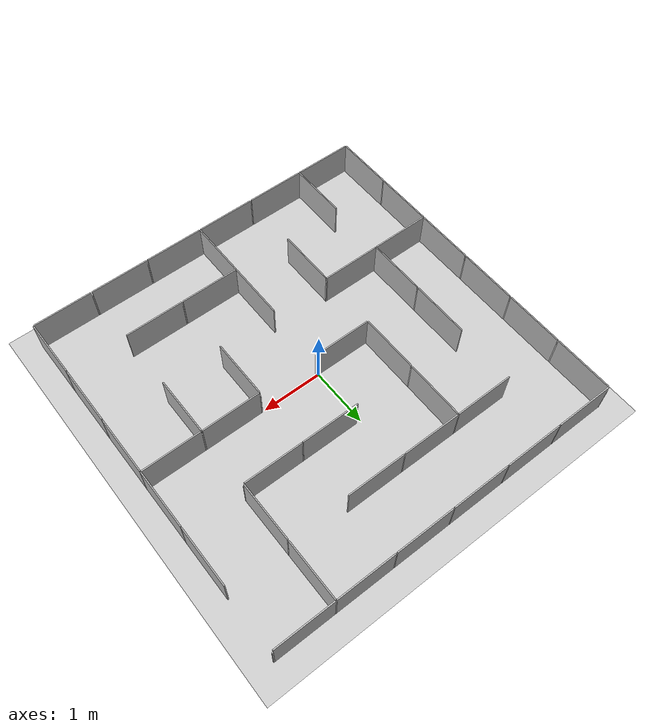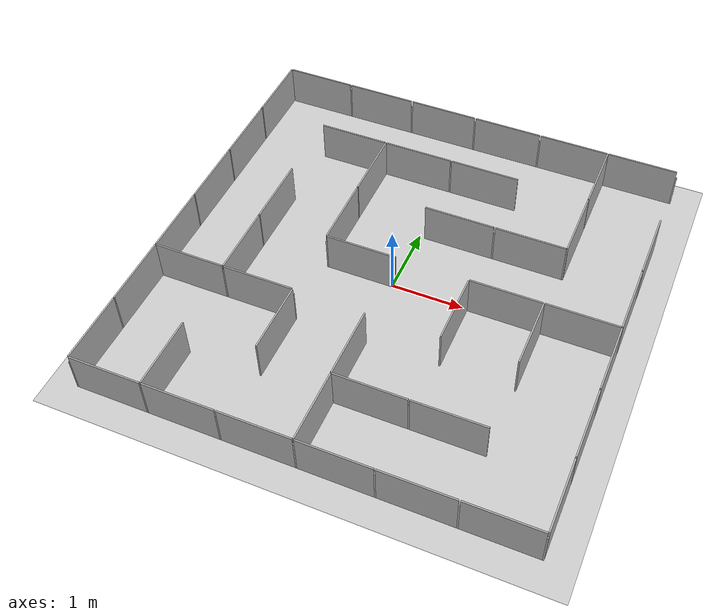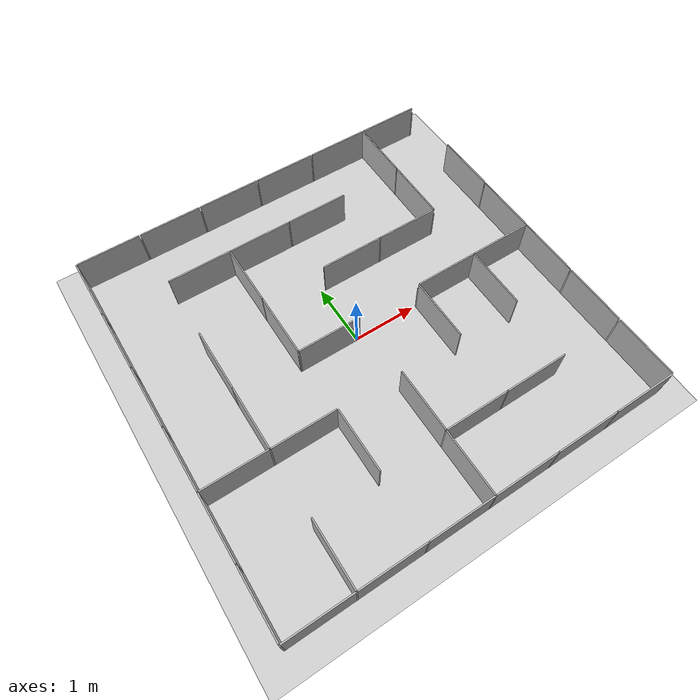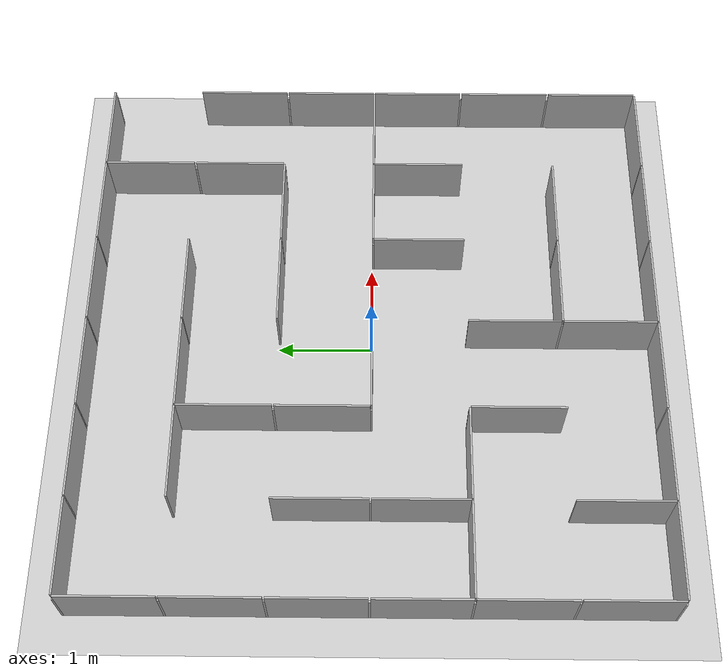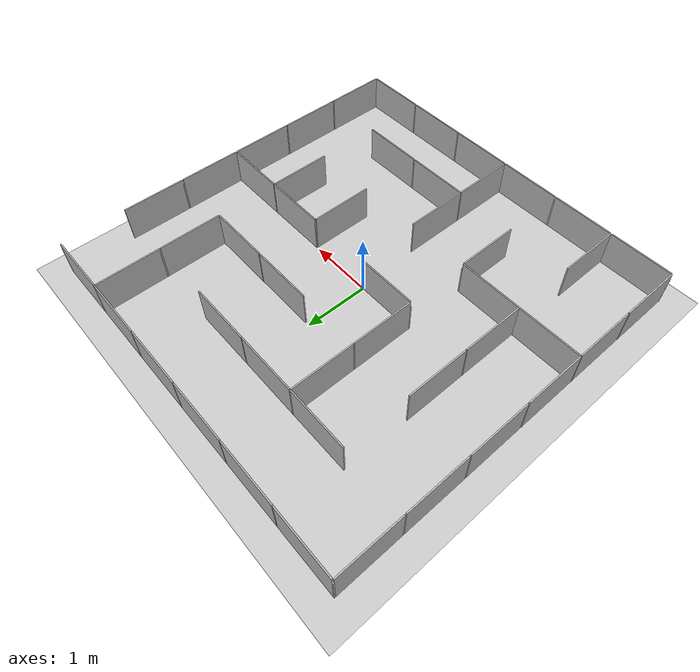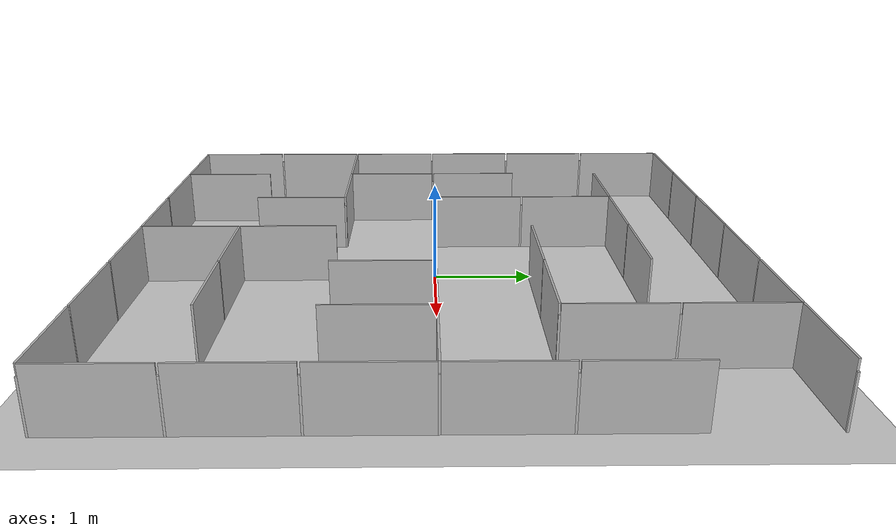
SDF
<sdf version="1.7">
 <world name="default">
  <light name="sun" type="directional">
   <pose>0 0 10 0 -0 0</pose>
   <diffuse>0.8 0.8 0.8 1</diffuse>
   <specular>0.2 0.2 0.2 1</specular>
   <attenuation>
    <range>1000</range>
    <constant>0.9</constant>
    <linear>0.01</linear>
    <quadratic>0.001</quadratic>
   </attenuation>
   <direction>-0.5 0.1 -0.9</direction>
   <spot><inner_angle>0</inner_angle><outer_angle>0</outer_angle><falloff>0</falloff></spot>
  </light>
  <model name="ground_plane">
   <static>1</static>
   <link name="link">
    <collision name="collision">
     <geometry><plane><normal>0 0 1</normal><size>100 100</size></plane></geometry>
     <surface><friction><ode><mu>100</mu><mu2>50</mu2></ode></friction></surface>
    </collision>
    <visual name="visual">
     <cast_shadows>0</cast_shadows>
     <geometry><plane><normal>0 0 1</normal><size>100 100</size></plane></geometry>
     <material>
      <script><uri>file://media/materials/scripts/gazebo.material</uri><name>Gazebo/Grey</name></script>
     </material>
    </visual>
   </link>
  </model>
  <gravity>0 0 -9.8</gravity>
  <magnetic_field>6e-06 2.3e-05 -4.2e-05</magnetic_field>
  <atmosphere type="adiabatic"/>
  <physics type="ode">
   <max_step_size>0.001</max_step_size>
   <real_time_factor>1</real_time_factor>
   <real_time_update_rate>1000</real_time_update_rate>
  </physics>
  <scene><ambient>0.4 0.4 0.4 1</ambient><background>0.7 0.7 0.7 1</background><shadows>1</shadows></scene>
  <audio><device>default</device></audio>
  <spherical_coordinates>
   <surface_model>EARTH_WGS84</surface_model>
   <latitude_deg>0</latitude_deg>
   <longitude_deg>0</longitude_deg>
   <elevation>0</elevation>
   <heading_deg>0</heading_deg>
  </spherical_coordinates>
  <model name="maze_4_metal_6x6">
   <frame name="metal_plate_0_0_b::__model__" attached_to="metal_plate_0_0_b::main">
    <pose relative_to="__model__">0 0 0 0 -0 1.571</pose>
   </frame>
   <static>1</static>
   <link name="metal_plate_0_0_b::main">
    <pose relative_to="metal_plate_0_0_b::__model__">0 0 0 0 -0 0</pose>
    <collision name="collision">
     <pose>0 -0.5 0.3 -1.571 -0 -1.571</pose>
     <geometry><box><size>0.98 0.6 0.02</size></box></geometry>
    </collision>
    <visual name="visual">
     <pose>0.01 -0.01 0 3.14159 -1.57059 3.14159</pose>
     <geometry><mesh><scale>1 1 1</scale><uri>model://metal_plate/meshes/metal_plate.dae</uri></mesh></geometry>
    </visual>
   </link>
   <frame name="metal_joint_0_0_b::__model__" attached_to="metal_joint_0_0_b::link">
    <pose relative_to="__model__">0 0 0 0 -0 0</pose>
   </frame>
   <static>1</static>
   <link name="metal_joint_0_0_b::link">
    <pose relative_to="metal_joint_0_0_b::__model__">0 0 0.25 0 -0 0</pose>
    <collision name="metal_joint_01"><geometry><box><size>0.02 0.02 0.5</size></box></geometry></collision>
    <visual name="visual_metal_joint_0">
     <geometry><box><size>0.02 0.02 0.5</size></box></geometry>
     <material>
      <script>
       <uri>model://metal_joint/materials/scripts</uri>
       <uri>model://metal_joint/materials/textures</uri>
       <name>metal_joint</name>
      </script>
     </material>
    </visual>
   </link>
   <frame name="metal_plate_1_0_b::__model__" attached_to="metal_plate_1_0_b::main">
    <pose relative_to="__model__">1 0 0 0 -0 1.571</pose>
   </frame>
   <static>1</static>
   <link name="metal_plate_1_0_b::main">
    <pose relative_to="metal_plate_1_0_b::__model__">0 0 0 0 -0 0</pose>
    <collision name="collision">
     <pose>0 -0.5 0.3 -1.571 -0 -1.571</pose>
     <geometry><box><size>0.98 0.6 0.02</size></box></geometry>
    </collision>
    <visual name="visual">
     <pose>0.01 -0.01 0 3.14159 -1.57059 3.14159</pose>
     <geometry><mesh><scale>1 1 1</scale><uri>model://metal_plate/meshes/metal_plate.dae</uri></mesh></geometry>
    </visual>
   </link>
   <frame name="metal_joint_1_0_b::__model__" attached_to="metal_joint_1_0_b::link">
    <pose relative_to="__model__">1 0 0 0 -0 0</pose>
   </frame>
   <static>1</static>
   <link name="metal_joint_1_0_b::link">
    <pose relative_to="metal_joint_1_0_b::__model__">0 0 0.25 0 -0 0</pose>
    <collision name="metal_joint_01"><geometry><box><size>0.02 0.02 0.5</size></box></geometry></collision>
    <visual name="visual_metal_joint_0">
     <geometry><box><size>0.02 0.02 0.5</size></box></geometry>
     <material>
      <script>
       <uri>model://metal_joint/materials/scripts</uri>
       <uri>model://metal_joint/materials/textures</uri>
       <name>metal_joint</name>
      </script>
     </material>
    </visual>
   </link>
   <frame name="metal_plate_2_0_b::__model__" attached_to="metal_plate_2_0_b::main">
    <pose relative_to="__model__">2 0 0 0 -0 1.571</pose>
   </frame>
   <static>1</static>
   <link name="metal_plate_2_0_b::main">
    <pose relative_to="metal_plate_2_0_b::__model__">0 0 0 0 -0 0</pose>
    <collision name="collision">
     <pose>0 -0.5 0.3 -1.571 -0 -1.571</pose>
     <geometry><box><size>0.98 0.6 0.02</size></box></geometry>
    </collision>
    <visual name="visual">
     <pose>0.01 -0.01 0 3.14159 -1.57059 3.14159</pose>
     <geometry><mesh><scale>1 1 1</scale><uri>model://metal_plate/meshes/metal_plate.dae</uri></mesh></geometry>
    </visual>
   </link>
   <frame name="metal_joint_2_0_b::__model__" attached_to="metal_joint_2_0_b::link">
    <pose relative_to="__model__">2 0 0 0 -0 0</pose>
   </frame>
   <static>1</static>
   <link name="metal_joint_2_0_b::link">
    <pose relative_to="metal_joint_2_0_b::__model__">0 0 0.25 0 -0 0</pose>
    <collision name="metal_joint_01"><geometry><box><size>0.02 0.02 0.5</size></box></geometry></collision>
    <visual name="visual_metal_joint_0">
     <geometry><box><size>0.02 0.02 0.5</size></box></geometry>
     <material>
      <script>
       <uri>model://metal_joint/materials/scripts</uri>
       <uri>model://metal_joint/materials/textures</uri>
       <name>metal_joint</name>
      </script>
     </material>
    </visual>
   </link>
   <frame name="metal_plate_3_0_b::__model__" attached_to="metal_plate_3_0_b::main">
    <pose relative_to="__model__">3 0 0 0 -0 1.571</pose>
   </frame>
   <static>1</static>
   <link name="metal_plate_3_0_b::main">
    <pose relative_to="metal_plate_3_0_b::__model__">0 0 0 0 -0 0</pose>
    <collision name="collision">
     <pose>0 -0.5 0.3 -1.571 -0 -1.571</pose>
     <geometry><box><size>0.98 0.6 0.02</size></box></geometry>
    </collision>
    <visual name="visual">
     <pose>0.01 -0.01 0 3.14159 -1.57059 3.14159</pose>
     <geometry><mesh><scale>1 1 1</scale><uri>model://metal_plate/meshes/metal_plate.dae</uri></mesh></geometry>
    </visual>
   </link>
   <frame name="metal_joint_3_0_b::__model__" attached_to="metal_joint_3_0_b::link">
    <pose relative_to="__model__">3 0 0 0 -0 0</pose>
   </frame>
   <static>1</static>
   <link name="metal_joint_3_0_b::link">
    <pose relative_to="metal_joint_3_0_b::__model__">0 0 0.25 0 -0 0</pose>
    <collision name="metal_joint_01"><geometry><box><size>0.02 0.02 0.5</size></box></geometry></collision>
    <visual name="visual_metal_joint_0">
     <geometry><box><size>0.02 0.02 0.5</size></box></geometry>
     <material>
      <script>
       <uri>model://metal_joint/materials/scripts</uri>
       <uri>model://metal_joint/materials/textures</uri>
       <name>metal_joint</name>
      </script>
     </material>
    </visual>
   </link>
   <frame name="metal_plate_4_0_b::__model__" attached_to="metal_plate_4_0_b::main">
    <pose relative_to="__model__">4 0 0 0 -0 1.571</pose>
   </frame>
   <static>1</static>
   <link name="metal_plate_4_0_b::main">
    <pose relative_to="metal_plate_4_0_b::__model__">0 0 0 0 -0 0</pose>
    <collision name="collision">
     <pose>0 -0.5 0.3 -1.571 -0 -1.571</pose>
     <geometry><box><size>0.98 0.6 0.02</size></box></geometry>
    </collision>
    <visual name="visual">
     <pose>0.01 -0.01 0 3.14159 -1.57059 3.14159</pose>
     <geometry><mesh><scale>1 1 1</scale><uri>model://metal_plate/meshes/metal_plate.dae</uri></mesh></geometry>
    </visual>
   </link>
   <frame name="metal_joint_4_0_b::__model__" attached_to="metal_joint_4_0_b::link">
    <pose relative_to="__model__">4 0 0 0 -0 0</pose>
   </frame>
   <static>1</static>
   <link name="metal_joint_4_0_b::link">
    <pose relative_to="metal_joint_4_0_b::__model__">0 0 0.25 0 -0 0</pose>
    <collision name="metal_joint_01"><geometry><box><size>0.02 0.02 0.5</size></box></geometry></collision>
    <visual name="visual_metal_joint_0">
     <geometry><box><size>0.02 0.02 0.5</size></box></geometry>
     <material>
      <script>
       <uri>model://metal_joint/materials/scripts</uri>
       <uri>model://metal_joint/materials/textures</uri>
       <name>metal_joint</name>
      </script>
     </material>
    </visual>
   </link>
   <frame name="metal_plate_5_0_b::__model__" attached_to="metal_plate_5_0_b::main">
    <pose relative_to="__model__">5 0 0 0 -0 1.571</pose>
   </frame>
   <static>1</static>
   <link name="metal_plate_5_0_b::main">
    <pose relative_to="metal_plate_5_0_b::__model__">0 0 0 0 -0 0</pose>
    <collision name="collision">
     <pose>0 -0.5 0.3 -1.571 -0 -1.571</pose>
     <geometry><box><size>0.98 0.6 0.02</size></box></geometry>
    </collision>
    <visual name="visual">
     <pose>0.01 -0.01 0 3.14159 -1.57059 3.14159</pose>
     <geometry><mesh><scale>1 1 1</scale><uri>model://metal_plate/meshes/metal_plate.dae</uri></mesh></geometry>
    </visual>
   </link>
   <frame name="metal_joint_5_0_b::__model__" attached_to="metal_joint_5_0_b::link">
    <pose relative_to="__model__">5 0 0 0 -0 0</pose>
   </frame>
   <static>1</static>
   <link name="metal_joint_5_0_b::link">
    <pose relative_to="metal_joint_5_0_b::__model__">0 0 0.25 0 -0 0</pose>
    <collision name="metal_joint_01"><geometry><box><size>0.02 0.02 0.5</size></box></geometry></collision>
    <visual name="visual_metal_joint_0">
     <geometry><box><size>0.02 0.02 0.5</size></box></geometry>
     <material>
      <script>
       <uri>model://metal_joint/materials/scripts</uri>
       <uri>model://metal_joint/materials/textures</uri>
       <name>metal_joint</name>
      </script>
     </material>
    </visual>
   </link>
   <frame name="metal_plate_0_6_b::__model__" attached_to="metal_plate_0_6_b::main">
    <pose relative_to="__model__">0 6 0 0 -0 1.571</pose>
   </frame>
   <static>1</static>
   <link name="metal_plate_0_6_b::main">
    <pose relative_to="metal_plate_0_6_b::__model__">0 0 0 0 -0 0</pose>
    <collision name="collision">
     <pose>0 -0.5 0.3 -1.571 -0 -1.571</pose>
     <geometry><box><size>0.98 0.6 0.02</size></box></geometry>
    </collision>
    <visual name="visual">
     <pose>0.01 -0.01 0 3.14159 -1.57059 3.14159</pose>
     <geometry><mesh><scale>1 1 1</scale><uri>model://metal_plate/meshes/metal_plate.dae</uri></mesh></geometry>
    </visual>
   </link>
   <frame name="metal_joint_0_6_b::__model__" attached_to="metal_joint_0_6_b::link">
    <pose relative_to="__model__">0 6 0 0 -0 0</pose>
   </frame>
   <static>1</static>
   <link name="metal_joint_0_6_b::link">
    <pose relative_to="metal_joint_0_6_b::__model__">0 0 0.25 0 -0 0</pose>
    <collision name="metal_joint_01"><geometry><box><size>0.02 0.02 0.5</size></box></geometry></collision>
    <visual name="visual_metal_joint_0">
     <geometry><box><size>0.02 0.02 0.5</size></box></geometry>
     <material>
      <script>
       <uri>model://metal_joint/materials/scripts</uri>
       <uri>model://metal_joint/materials/textures</uri>
       <name>metal_joint</name>
      </script>
     </material>
    </visual>
   </link>
   <frame name="metal_plate_1_6_b::__model__" attached_to="metal_plate_1_6_b::main">
    <pose relative_to="__model__">1 6 0 0 -0 1.571</pose>
   </frame>
   <static>1</static>
   <link name="metal_plate_1_6_b::main">
    <pose relative_to="metal_plate_1_6_b::__model__">0 0 0 0 -0 0</pose>
    <collision name="collision">
     <pose>0 -0.5 0.3 -1.571 -0 -1.571</pose>
     <geometry><box><size>0.98 0.6 0.02</size></box></geometry>
    </collision>
    <visual name="visual">
     <pose>0.01 -0.01 0 3.14159 -1.57059 3.14159</pose>
     <geometry><mesh><scale>1 1 1</scale><uri>model://metal_plate/meshes/metal_plate.dae</uri></mesh></geometry>
    </visual>
   </link>
   <frame name="metal_joint_1_6_b::__model__" attached_to="metal_joint_1_6_b::link">
    <pose relative_to="__model__">1 6 0 0 -0 0</pose>
   </frame>
   <static>1</static>
   <link name="metal_joint_1_6_b::link">
    <pose relative_to="metal_joint_1_6_b::__model__">0 0 0.25 0 -0 0</pose>
    <collision name="metal_joint_01"><geometry><box><size>0.02 0.02 0.5</size></box></geometry></collision>
    <visual name="visual_metal_joint_0">
     <geometry><box><size>0.02 0.02 0.5</size></box></geometry>
     <material>
      <script>
       <uri>model://metal_joint/materials/scripts</uri>
       <uri>model://metal_joint/materials/textures</uri>
       <name>metal_joint</name>
      </script>
     </material>
    </visual>
   </link>
   <frame name="metal_plate_2_6_b::__model__" attached_to="metal_plate_2_6_b::main">
    <pose relative_to="__model__">2 6 0 0 -0 1.571</pose>
   </frame>
   <static>1</static>
   <link name="metal_plate_2_6_b::main">
    <pose relative_to="metal_plate_2_6_b::__model__">0 0 0 0 -0 0</pose>
    <collision name="collision">
     <pose>0 -0.5 0.3 -1.571 -0 -1.571</pose>
     <geometry><box><size>0.98 0.6 0.02</size></box></geometry>
    </collision>
    <visual name="visual">
     <pose>0.01 -0.01 0 3.14159 -1.57059 3.14159</pose>
     <geometry><mesh><scale>1 1 1</scale><uri>model://metal_plate/meshes/metal_plate.dae</uri></mesh></geometry>
    </visual>
   </link>
   <frame name="metal_joint_2_6_b::__model__" attached_to="metal_joint_2_6_b::link">
    <pose relative_to="__model__">2 6 0 0 -0 0</pose>
   </frame>
   <static>1</static>
   <link name="metal_joint_2_6_b::link">
    <pose relative_to="metal_joint_2_6_b::__model__">0 0 0.25 0 -0 0</pose>
    <collision name="metal_joint_01"><geometry><box><size>0.02 0.02 0.5</size></box></geometry></collision>
    <visual name="visual_metal_joint_0">
     <geometry><box><size>0.02 0.02 0.5</size></box></geometry>
     <material>
      <script>
       <uri>model://metal_joint/materials/scripts</uri>
       <uri>model://metal_joint/materials/textures</uri>
       <name>metal_joint</name>
      </script>
     </material>
    </visual>
   </link>
   <frame name="metal_plate_3_6_b::__model__" attached_to="metal_plate_3_6_b::main">
    <pose relative_to="__model__">3 6 0 0 -0 1.571</pose>
   </frame>
   <static>1</static>
   <link name="metal_plate_3_6_b::main">
    <pose relative_to="metal_plate_3_6_b::__model__">0 0 0 0 -0 0</pose>
    <collision name="collision">
     <pose>0 -0.5 0.3 -1.571 -0 -1.571</pose>
     <geometry><box><size>0.98 0.6 0.02</size></box></geometry>
    </collision>
    <visual name="visual">
     <pose>0.01 -0.01 0 3.14159 -1.57059 3.14159</pose>
     <geometry><mesh><scale>1 1 1</scale><uri>model://metal_plate/meshes/metal_plate.dae</uri></mesh></geometry>
    </visual>
   </link>
   <frame name="metal_joint_3_6_b::__model__" attached_to="metal_joint_3_6_b::link">
    <pose relative_to="__model__">3 6 0 0 -0 0</pose>
   </frame>
   <static>1</static>
   <link name="metal_joint_3_6_b::link">
    <pose relative_to="metal_joint_3_6_b::__model__">0 0 0.25 0 -0 0</pose>
    <collision name="metal_joint_01"><geometry><box><size>0.02 0.02 0.5</size></box></geometry></collision>
    <visual name="visual_metal_joint_0">
     <geometry><box><size>0.02 0.02 0.5</size></box></geometry>
     <material>
      <script>
       <uri>model://metal_joint/materials/scripts</uri>
       <uri>model://metal_joint/materials/textures</uri>
       <name>metal_joint</name>
      </script>
     </material>
    </visual>
   </link>
   <frame name="metal_plate_4_6_b::__model__" attached_to="metal_plate_4_6_b::main">
    <pose relative_to="__model__">4 6 0 0 -0 1.571</pose>
   </frame>
   <static>1</static>
   <link name="metal_plate_4_6_b::main">
    <pose relative_to="metal_plate_4_6_b::__model__">0 0 0 0 -0 0</pose>
    <collision name="collision">
     <pose>0 -0.5 0.3 -1.571 -0 -1.571</pose>
     <geometry><box><size>0.98 0.6 0.02</size></box></geometry>
    </collision>
    <visual name="visual">
     <pose>0.01 -0.01 0 3.14159 -1.57059 3.14159</pose>
     <geometry><mesh><scale>1 1 1</scale><uri>model://metal_plate/meshes/metal_plate.dae</uri></mesh></geometry>
    </visual>
   </link>
   <frame name="metal_joint_4_6_b::__model__" attached_to="metal_joint_4_6_b::link">
    <pose relative_to="__model__">4 6 0 0 -0 0</pose>
   </frame>
   <static>1</static>
   <link name="metal_joint_4_6_b::link">
    <pose relative_to="metal_joint_4_6_b::__model__">0 0 0.25 0 -0 0</pose>
    <collision name="metal_joint_01"><geometry><box><size>0.02 0.02 0.5</size></box></geometry></collision>
    <visual name="visual_metal_joint_0">
     <geometry><box><size>0.02 0.02 0.5</size></box></geometry>
     <material>
      <script>
       <uri>model://metal_joint/materials/scripts</uri>
       <uri>model://metal_joint/materials/textures</uri>
       <name>metal_joint</name>
      </script>
     </material>
    </visual>
   </link>
   <frame name="metal_plate_5_6_b::__model__" attached_to="metal_plate_5_6_b::main">
    <pose relative_to="__model__">5 6 0 0 -0 1.571</pose>
   </frame>
   <static>1</static>
   <link name="metal_plate_5_6_b::main">
    <pose relative_to="metal_plate_5_6_b::__model__">0 0 0 0 -0 0</pose>
    <collision name="collision">
     <pose>0 -0.5 0.3 -1.571 -0 -1.571</pose>
     <geometry><box><size>0.98 0.6 0.02</size></box></geometry>
    </collision>
    <visual name="visual">
     <pose>0.01 -0.01 0 3.14159 -1.57059 3.14159</pose>
     <geometry><mesh><scale>1 1 1</scale><uri>model://metal_plate/meshes/metal_plate.dae</uri></mesh></geometry>
    </visual>
   </link>
   <frame name="metal_joint_5_6_b::__model__" attached_to="metal_joint_5_6_b::link">
    <pose relative_to="__model__">5 6 0 0 -0 0</pose>
   </frame>
   <static>1</static>
   <link name="metal_joint_5_6_b::link">
    <pose relative_to="metal_joint_5_6_b::__model__">0 0 0.25 0 -0 0</pose>
    <collision name="metal_joint_01"><geometry><box><size>0.02 0.02 0.5</size></box></geometry></collision>
    <visual name="visual_metal_joint_0">
     <geometry><box><size>0.02 0.02 0.5</size></box></geometry>
     <material>
      <script>
       <uri>model://metal_joint/materials/scripts</uri>
       <uri>model://metal_joint/materials/textures</uri>
       <name>metal_joint</name>
      </script>
     </material>
    </visual>
   </link>
   <frame name="metal_plate_0_0_a::__model__" attached_to="metal_plate_0_0_a::main">
    <pose relative_to="__model__">0 0 0 0 -0 3.14159</pose>
   </frame>
   <static>1</static>
   <link name="metal_plate_0_0_a::main">
    <pose relative_to="metal_plate_0_0_a::__model__">0 0 0 0 -0 0</pose>
    <collision name="collision">
     <pose>0 -0.5 0.3 -1.571 -0 -1.571</pose>
     <geometry><box><size>0.98 0.6 0.02</size></box></geometry>
    </collision>
    <visual name="visual">
     <pose>0.01 -0.01 0 3.14159 -1.57059 3.14159</pose>
     <geometry><mesh><scale>1 1 1</scale><uri>model://metal_plate/meshes/metal_plate.dae</uri></mesh></geometry>
    </visual>
   </link>
   <frame name="metal_joint_6_6_a::__model__" attached_to="metal_joint_6_6_a::link">
    <pose relative_to="__model__">6 6 0 0 -0 0</pose>
   </frame>
   <static>1</static>
   <link name="metal_joint_6_6_a::link">
    <pose relative_to="metal_joint_6_6_a::__model__">0 0 0.25 0 -0 0</pose>
    <collision name="metal_joint_01"><geometry><box><size>0.02 0.02 0.5</size></box></geometry></collision>
    <visual name="visual_metal_joint_0">
     <geometry><box><size>0.02 0.02 0.5</size></box></geometry>
     <material>
      <script>
       <uri>model://metal_joint/materials/scripts</uri>
       <uri>model://metal_joint/materials/textures</uri>
       <name>metal_joint</name>
      </script>
     </material>
    </visual>
   </link>
   <frame name="metal_plate_0_1_a::__model__" attached_to="metal_plate_0_1_a::main">
    <pose relative_to="__model__">0 1 0 0 -0 3.14159</pose>
   </frame>
   <static>1</static>
   <link name="metal_plate_0_1_a::main">
    <pose relative_to="metal_plate_0_1_a::__model__">0 0 0 0 -0 0</pose>
    <collision name="collision">
     <pose>0 -0.5 0.3 -1.571 -0 -1.571</pose>
     <geometry><box><size>0.98 0.6 0.02</size></box></geometry>
    </collision>
    <visual name="visual">
     <pose>0.01 -0.01 0 3.14159 -1.57059 3.14159</pose>
     <geometry><mesh><scale>1 1 1</scale><uri>model://metal_plate/meshes/metal_plate.dae</uri></mesh></geometry>
    </visual>
   </link>
   <frame name="metal_joint_0_1_a::__model__" attached_to="metal_joint_0_1_a::link">
    <pose relative_to="__model__">0 1 0 0 -0 0</pose>
   </frame>
   <static>1</static>
   <link name="metal_joint_0_1_a::link">
    <pose relative_to="metal_joint_0_1_a::__model__">0 0 0.25 0 -0 0</pose>
    <collision name="metal_joint_01"><geometry><box><size>0.02 0.02 0.5</size></box></geometry></collision>
    <visual name="visual_metal_joint_0">
     <geometry><box><size>0.02 0.02 0.5</size></box></geometry>
     <material>
      <script>
       <uri>model://metal_joint/materials/scripts</uri>
       <uri>model://metal_joint/materials/textures</uri>
       <name>metal_joint</name>
      </script>
     </material>
    </visual>
   </link>
   <frame name="metal_plate_0_2_a::__model__" attached_to="metal_plate_0_2_a::main">
    <pose relative_to="__model__">0 2 0 0 -0 3.14159</pose>
   </frame>
   <static>1</static>
   <link name="metal_plate_0_2_a::main">
    <pose relative_to="metal_plate_0_2_a::__model__">0 0 0 0 -0 0</pose>
    <collision name="collision">
     <pose>0 -0.5 0.3 -1.571 -0 -1.571</pose>
     <geometry><box><size>0.98 0.6 0.02</size></box></geometry>
    </collision>
    <visual name="visual">
     <pose>0.01 -0.01 0 3.14159 -1.57059 3.14159</pose>
     <geometry><mesh><scale>1 1 1</scale><uri>model://metal_plate/meshes/metal_plate.dae</uri></mesh></geometry>
    </visual>
   </link>
   <frame name="metal_joint_0_2_a::__model__" attached_to="metal_joint_0_2_a::link">
    <pose relative_to="__model__">0 2 0 0 -0 0</pose>
   </frame>
   <static>1</static>
   <link name="metal_joint_0_2_a::link">
    <pose relative_to="metal_joint_0_2_a::__model__">0 0 0.25 0 -0 0</pose>
    <collision name="metal_joint_01"><geometry><box><size>0.02 0.02 0.5</size></box></geometry></collision>
    <visual name="visual_metal_joint_0">
     <geometry><box><size>0.02 0.02 0.5</size></box></geometry>
     <material>
      <script>
       <uri>model://metal_joint/materials/scripts</uri>
       <uri>model://metal_joint/materials/textures</uri>
       <name>metal_joint</name>
      </script>
     </material>
    </visual>
   </link>
   <frame name="metal_plate_0_3_a::__model__" attached_to="metal_plate_0_3_a::main">
    <pose relative_to="__model__">0 3 0 0 -0 3.14159</pose>
   </frame>
   <static>1</static>
   <link name="metal_plate_0_3_a::main">
    <pose relative_to="metal_plate_0_3_a::__model__">0 0 0 0 -0 0</pose>
    <collision name="collision">
     <pose>0 -0.5 0.3 -1.571 -0 -1.571</pose>
     <geometry><box><size>0.98 0.6 0.02</size></box></geometry>
    </collision>
    <visual name="visual">
     <pose>0.01 -0.01 0 3.14159 -1.57059 3.14159</pose>
     <geometry><mesh><scale>1 1 1</scale><uri>model://metal_plate/meshes/metal_plate.dae</uri></mesh></geometry>
    </visual>
   </link>
   <frame name="metal_joint_0_3_a::__model__" attached_to="metal_joint_0_3_a::link">
    <pose relative_to="__model__">0 3 0 0 -0 0</pose>
   </frame>
   <static>1</static>
   <link name="metal_joint_0_3_a::link">
    <pose relative_to="metal_joint_0_3_a::__model__">0 0 0.25 0 -0 0</pose>
    <collision name="metal_joint_01"><geometry><box><size>0.02 0.02 0.5</size></box></geometry></collision>
    <visual name="visual_metal_joint_0">
     <geometry><box><size>0.02 0.02 0.5</size></box></geometry>
     <material>
      <script>
       <uri>model://metal_joint/materials/scripts</uri>
       <uri>model://metal_joint/materials/textures</uri>
       <name>metal_joint</name>
      </script>
     </material>
    </visual>
   </link>
   <frame name="metal_plate_0_4_a::__model__" attached_to="metal_plate_0_4_a::main">
    <pose relative_to="__model__">0 4 0 0 -0 3.14159</pose>
   </frame>
   <static>1</static>
   <link name="metal_plate_0_4_a::main">
    <pose relative_to="metal_plate_0_4_a::__model__">0 0 0 0 -0 0</pose>
    <collision name="collision">
     <pose>0 -0.5 0.3 -1.571 -0 -1.571</pose>
     <geometry><box><size>0.98 0.6 0.02</size></box></geometry>
    </collision>
    <visual name="visual">
     <pose>0.01 -0.01 0 3.14159 -1.57059 3.14159</pose>
     <geometry><mesh><scale>1 1 1</scale><uri>model://metal_plate/meshes/metal_plate.dae</uri></mesh></geometry>
    </visual>
   </link>
   <frame name="metal_joint_0_4_a::__model__" attached_to="metal_joint_0_4_a::link">
    <pose relative_to="__model__">0 4 0 0 -0 0</pose>
   </frame>
   <static>1</static>
   <link name="metal_joint_0_4_a::link">
    <pose relative_to="metal_joint_0_4_a::__model__">0 0 0.25 0 -0 0</pose>
    <collision name="metal_joint_01"><geometry><box><size>0.02 0.02 0.5</size></box></geometry></collision>
    <visual name="visual_metal_joint_0">
     <geometry><box><size>0.02 0.02 0.5</size></box></geometry>
     <material>
      <script>
       <uri>model://metal_joint/materials/scripts</uri>
       <uri>model://metal_joint/materials/textures</uri>
       <name>metal_joint</name>
      </script>
     </material>
    </visual>
   </link>
   <frame name="metal_plate_0_5_a::__model__" attached_to="metal_plate_0_5_a::main">
    <pose relative_to="__model__">0 5 0 0 -0 3.14159</pose>
   </frame>
   <static>1</static>
   <link name="metal_plate_0_5_a::main">
    <pose relative_to="metal_plate_0_5_a::__model__">0 0 0 0 -0 0</pose>
    <collision name="collision">
     <pose>0 -0.5 0.3 -1.571 -0 -1.571</pose>
     <geometry><box><size>0.98 0.6 0.02</size></box></geometry>
    </collision>
    <visual name="visual">
     <pose>0.01 -0.01 0 3.14159 -1.57059 3.14159</pose>
     <geometry><mesh><scale>1 1 1</scale><uri>model://metal_plate/meshes/metal_plate.dae</uri></mesh></geometry>
    </visual>
   </link>
   <frame name="metal_joint_0_5_a::__model__" attached_to="metal_joint_0_5_a::link">
    <pose relative_to="__model__">0 5 0 0 -0 0</pose>
   </frame>
   <static>1</static>
   <link name="metal_joint_0_5_a::link">
    <pose relative_to="metal_joint_0_5_a::__model__">0 0 0.25 0 -0 0</pose>
    <collision name="metal_joint_01"><geometry><box><size>0.02 0.02 0.5</size></box></geometry></collision>
    <visual name="visual_metal_joint_0">
     <geometry><box><size>0.02 0.02 0.5</size></box></geometry>
     <material>
      <script>
       <uri>model://metal_joint/materials/scripts</uri>
       <uri>model://metal_joint/materials/textures</uri>
       <name>metal_joint</name>
      </script>
     </material>
    </visual>
   </link>
   <frame name="metal_plate_6_0_a::__model__" attached_to="metal_plate_6_0_a::main">
    <pose relative_to="__model__">6 0 0 0 -0 3.14159</pose>
   </frame>
   <static>1</static>
   <link name="metal_plate_6_0_a::main">
    <pose relative_to="metal_plate_6_0_a::__model__">0 0 0 0 -0 0</pose>
    <collision name="collision">
     <pose>0 -0.5 0.3 -1.571 -0 -1.571</pose>
     <geometry><box><size>0.98 0.6 0.02</size></box></geometry>
    </collision>
    <visual name="visual">
     <pose>0.01 -0.01 0 3.14159 -1.57059 3.14159</pose>
     <geometry><mesh><scale>1 1 1</scale><uri>model://metal_plate/meshes/metal_plate.dae</uri></mesh></geometry>
    </visual>
   </link>
   <frame name="metal_joint_6_0_a::__model__" attached_to="metal_joint_6_0_a::link">
    <pose relative_to="__model__">6 0 0 0 -0 0</pose>
   </frame>
   <static>1</static>
   <link name="metal_joint_6_0_a::link">
    <pose relative_to="metal_joint_6_0_a::__model__">0 0 0.25 0 -0 0</pose>
    <collision name="metal_joint_01"><geometry><box><size>0.02 0.02 0.5</size></box></geometry></collision>
    <visual name="visual_metal_joint_0">
     <geometry><box><size>0.02 0.02 0.5</size></box></geometry>
     <material>
      <script>
       <uri>model://metal_joint/materials/scripts</uri>
       <uri>model://metal_joint/materials/textures</uri>
       <name>metal_joint</name>
      </script>
     </material>
    </visual>
   </link>
   <frame name="metal_plate_6_1_a::__model__" attached_to="metal_plate_6_1_a::main">
    <pose relative_to="__model__">6 1 0 0 -0 3.14159</pose>
   </frame>
   <static>1</static>
   <link name="metal_plate_6_1_a::main">
    <pose relative_to="metal_plate_6_1_a::__model__">0 0 0 0 -0 0</pose>
    <collision name="collision">
     <pose>0 -0.5 0.3 -1.571 -0 -1.571</pose>
     <geometry><box><size>0.98 0.6 0.02</size></box></geometry>
    </collision>
    <visual name="visual">
     <pose>0.01 -0.01 0 3.14159 -1.57059 3.14159</pose>
     <geometry><mesh><scale>1 1 1</scale><uri>model://metal_plate/meshes/metal_plate.dae</uri></mesh></geometry>
    </visual>
   </link>
   <frame name="metal_joint_6_1_a::__model__" attached_to="metal_joint_6_1_a::link">
    <pose relative_to="__model__">6 1 0 0 -0 0</pose>
   </frame>
   <static>1</static>
   <link name="metal_joint_6_1_a::link">
    <pose relative_to="metal_joint_6_1_a::__model__">0 0 0.25 0 -0 0</pose>
    <collision name="metal_joint_01"><geometry><box><size>0.02 0.02 0.5</size></box></geometry></collision>
    <visual name="visual_metal_joint_0">
     <geometry><box><size>0.02 0.02 0.5</size></box></geometry>
     <material>
      <script>
       <uri>model://metal_joint/materials/scripts</uri>
       <uri>model://metal_joint/materials/textures</uri>
       <name>metal_joint</name>
      </script>
     </material>
    </visual>
   </link>
   <frame name="metal_plate_6_2_a::__model__" attached_to="metal_plate_6_2_a::main">
    <pose relative_to="__model__">6 2 0 0 -0 3.14159</pose>
   </frame>
   <static>1</static>
   <link name="metal_plate_6_2_a::main">
    <pose relative_to="metal_plate_6_2_a::__model__">0 0 0 0 -0 0</pose>
    <collision name="collision">
     <pose>0 -0.5 0.3 -1.571 -0 -1.571</pose>
     <geometry><box><size>0.98 0.6 0.02</size></box></geometry>
    </collision>
    <visual name="visual">
     <pose>0.01 -0.01 0 3.14159 -1.57059 3.14159</pose>
     <geometry><mesh><scale>1 1 1</scale><uri>model://metal_plate/meshes/metal_plate.dae</uri></mesh></geometry>
    </visual>
   </link>
   <frame name="metal_joint_6_2_a::__model__" attached_to="metal_joint_6_2_a::link">
    <pose relative_to="__model__">6 2 0 0 -0 0</pose>
   </frame>
   <static>1</static>
   <link name="metal_joint_6_2_a::link">
    <pose relative_to="metal_joint_6_2_a::__model__">0 0 0.25 0 -0 0</pose>
    <collision name="metal_joint_01"><geometry><box><size>0.02 0.02 0.5</size></box></geometry></collision>
    <visual name="visual_metal_joint_0">
     <geometry><box><size>0.02 0.02 0.5</size></box></geometry>
     <material>
      <script>
       <uri>model://metal_joint/materials/scripts</uri>
       <uri>model://metal_joint/materials/textures</uri>
       <name>metal_joint</name>
      </script>
     </material>
    </visual>
   </link>
   <frame name="metal_plate_6_3_a::__model__" attached_to="metal_plate_6_3_a::main">
    <pose relative_to="__model__">6 3 0 0 -0 3.14159</pose>
   </frame>
   <static>1</static>
   <link name="metal_plate_6_3_a::main">
    <pose relative_to="metal_plate_6_3_a::__model__">0 0 0 0 -0 0</pose>
    <collision name="collision">
     <pose>0 -0.5 0.3 -1.571 -0 -1.571</pose>
     <geometry><box><size>0.98 0.6 0.02</size></box></geometry>
    </collision>
    <visual name="visual">
     <pose>0.01 -0.01 0 3.14159 -1.57059 3.14159</pose>
     <geometry><mesh><scale>1 1 1</scale><uri>model://metal_plate/meshes/metal_plate.dae</uri></mesh></geometry>
    </visual>
   </link>
   <frame name="metal_joint_6_3_a::__model__" attached_to="metal_joint_6_3_a::link">
    <pose relative_to="__model__">6 3 0 0 -0 0</pose>
   </frame>
   <static>1</static>
   <link name="metal_joint_6_3_a::link">
    <pose relative_to="metal_joint_6_3_a::__model__">0 0 0.25 0 -0 0</pose>
    <collision name="metal_joint_01"><geometry><box><size>0.02 0.02 0.5</size></box></geometry></collision>
    <visual name="visual_metal_joint_0">
     <geometry><box><size>0.02 0.02 0.5</size></box></geometry>
     <material>
      <script>
       <uri>model://metal_joint/materials/scripts</uri>
       <uri>model://metal_joint/materials/textures</uri>
       <name>metal_joint</name>
      </script>
     </material>
    </visual>
   </link>
   <frame name="metal_plate_6_4_a::__model__" attached_to="metal_plate_6_4_a::main">
    <pose relative_to="__model__">6 4 0 0 -0 3.14159</pose>
   </frame>
   <static>1</static>
   <link name="metal_plate_6_4_a::main">
    <pose relative_to="metal_plate_6_4_a::__model__">0 0 0 0 -0 0</pose>
    <collision name="collision">
     <pose>0 -0.5 0.3 -1.571 -0 -1.571</pose>
     <geometry><box><size>0.98 0.6 0.02</size></box></geometry>
    </collision>
    <visual name="visual">
     <pose>0.01 -0.01 0 3.14159 -1.57059 3.14159</pose>
     <geometry><mesh><scale>1 1 1</scale><uri>model://metal_plate/meshes/metal_plate.dae</uri></mesh></geometry>
    </visual>
   </link>
   <frame name="metal_joint_6_4_a::__model__" attached_to="metal_joint_6_4_a::link">
    <pose relative_to="__model__">6 4 0 0 -0 0</pose>
   </frame>
   <static>1</static>
   <link name="metal_joint_6_4_a::link">
    <pose relative_to="metal_joint_6_4_a::__model__">0 0 0.25 0 -0 0</pose>
    <collision name="metal_joint_01"><geometry><box><size>0.02 0.02 0.5</size></box></geometry></collision>
    <visual name="visual_metal_joint_0">
     <geometry><box><size>0.02 0.02 0.5</size></box></geometry>
     <material>
      <script>
       <uri>model://metal_joint/materials/scripts</uri>
       <uri>model://metal_joint/materials/textures</uri>
       <name>metal_joint</name>
      </script>
     </material>
    </visual>
   </link>
   <frame name="metal_plate_4_1_c::__model__" attached_to="metal_plate_4_1_c::main">
    <pose relative_to="__model__">4 1 0 0 0 -1.5708</pose>
   </frame>
   <static>1</static>
   <link name="metal_plate_4_1_c::main">
    <pose relative_to="metal_plate_4_1_c::__model__">0 0 0 0 -0 0</pose>
    <collision name="collision">
     <pose>0 -0.5 0.3 -1.571 -0 -1.571</pose>
     <geometry><box><size>0.98 0.6 0.02</size></box></geometry>
    </collision>
    <visual name="visual">
     <pose>0.01 -0.01 0 3.14159 -1.57059 3.14159</pose>
     <geometry><mesh><scale>1 1 1</scale><uri>model://metal_plate/meshes/metal_plate.dae</uri></mesh></geometry>
    </visual>
   </link>
   <frame name="metal_plate_5_1_c::__model__" attached_to="metal_plate_5_1_c::main">
    <pose relative_to="__model__">5 1 0 0 0 -1.5708</pose>
   </frame>
   <static>1</static>
   <link name="metal_plate_5_1_c::main">
    <pose relative_to="metal_plate_5_1_c::__model__">0 0 0 0 -0 0</pose>
    <collision name="collision">
     <pose>0 -0.5 0.3 -1.571 -0 -1.571</pose>
     <geometry><box><size>0.98 0.6 0.02</size></box></geometry>
    </collision>
    <visual name="visual">
     <pose>0.01 -0.01 0 3.14159 -1.57059 3.14159</pose>
     <geometry><mesh><scale>1 1 1</scale><uri>model://metal_plate/meshes/metal_plate.dae</uri></mesh></geometry>
    </visual>
   </link>
   <frame name="metal_plate_1_2_c::__model__" attached_to="metal_plate_1_2_c::main">
    <pose relative_to="__model__">1 2 0 0 0 -1.5708</pose>
   </frame>
   <static>1</static>
   <link name="metal_plate_1_2_c::main">
    <pose relative_to="metal_plate_1_2_c::__model__">0 0 0 0 -0 0</pose>
    <collision name="collision">
     <pose>0 -0.5 0.3 -1.571 -0 -1.571</pose>
     <geometry><box><size>0.98 0.6 0.02</size></box></geometry>
    </collision>
    <visual name="visual">
     <pose>0.01 -0.01 0 3.14159 -1.57059 3.14159</pose>
     <geometry><mesh><scale>1 1 1</scale><uri>model://metal_plate/meshes/metal_plate.dae</uri></mesh></geometry>
    </visual>
   </link>
   <frame name="metal_plate_2_2_c::__model__" attached_to="metal_plate_2_2_c::main">
    <pose relative_to="__model__">2 2 0 0 0 -1.5708</pose>
   </frame>
   <static>1</static>
   <link name="metal_plate_2_2_c::main">
    <pose relative_to="metal_plate_2_2_c::__model__">0 0 0 0 -0 0</pose>
    <collision name="collision">
     <pose>0 -0.5 0.3 -1.571 -0 -1.571</pose>
     <geometry><box><size>0.98 0.6 0.02</size></box></geometry>
    </collision>
    <visual name="visual">
     <pose>0.01 -0.01 0 3.14159 -1.57059 3.14159</pose>
     <geometry><mesh><scale>1 1 1</scale><uri>model://metal_plate/meshes/metal_plate.dae</uri></mesh></geometry>
    </visual>
   </link>
   <frame name="metal_plate_3_3_c::__model__" attached_to="metal_plate_3_3_c::main">
    <pose relative_to="__model__">3 3 0 0 0 -1.5708</pose>
   </frame>
   <static>1</static>
   <link name="metal_plate_3_3_c::main">
    <pose relative_to="metal_plate_3_3_c::__model__">0 0 0 0 -0 0</pose>
    <collision name="collision">
     <pose>0 -0.5 0.3 -1.571 -0 -1.571</pose>
     <geometry><box><size>0.98 0.6 0.02</size></box></geometry>
    </collision>
    <visual name="visual">
     <pose>0.01 -0.01 0 3.14159 -1.57059 3.14159</pose>
     <geometry><mesh><scale>1 1 1</scale><uri>model://metal_plate/meshes/metal_plate.dae</uri></mesh></geometry>
    </visual>
   </link>
   <frame name="metal_plate_5_3_c::__model__" attached_to="metal_plate_5_3_c::main">
    <pose relative_to="__model__">5 3 0 0 0 -1.5708</pose>
   </frame>
   <static>1</static>
   <link name="metal_plate_5_3_c::main">
    <pose relative_to="metal_plate_5_3_c::__model__">0 0 0 0 -0 0</pose>
    <collision name="collision">
     <pose>0 -0.5 0.3 -1.571 -0 -1.571</pose>
     <geometry><box><size>0.98 0.6 0.02</size></box></geometry>
    </collision>
    <visual name="visual">
     <pose>0.01 -0.01 0 3.14159 -1.57059 3.14159</pose>
     <geometry><mesh><scale>1 1 1</scale><uri>model://metal_plate/meshes/metal_plate.dae</uri></mesh></geometry>
    </visual>
   </link>
   <frame name="metal_plate_6_3_c::__model__" attached_to="metal_plate_6_3_c::main">
    <pose relative_to="__model__">6 3 0 0 0 -1.5708</pose>
   </frame>
   <static>1</static>
   <link name="metal_plate_6_3_c::main">
    <pose relative_to="metal_plate_6_3_c::__model__">0 0 0 0 -0 0</pose>
    <collision name="collision">
     <pose>0 -0.5 0.3 -1.571 -0 -1.571</pose>
     <geometry><box><size>0.98 0.6 0.02</size></box></geometry>
    </collision>
    <visual name="visual">
     <pose>0.01 -0.01 0 3.14159 -1.57059 3.14159</pose>
     <geometry><mesh><scale>1 1 1</scale><uri>model://metal_plate/meshes/metal_plate.dae</uri></mesh></geometry>
    </visual>
   </link>
   <frame name="metal_plate_4_4_c::__model__" attached_to="metal_plate_4_4_c::main">
    <pose relative_to="__model__">4 4 0 0 0 -1.5708</pose>
   </frame>
   <static>1</static>
   <link name="metal_plate_4_4_c::main">
    <pose relative_to="metal_plate_4_4_c::__model__">0 0 0 0 -0 0</pose>
    <collision name="collision">
     <pose>0 -0.5 0.3 -1.571 -0 -1.571</pose>
     <geometry><box><size>0.98 0.6 0.02</size></box></geometry>
    </collision>
    <visual name="visual">
     <pose>0.01 -0.01 0 3.14159 -1.57059 3.14159</pose>
     <geometry><mesh><scale>1 1 1</scale><uri>model://metal_plate/meshes/metal_plate.dae</uri></mesh></geometry>
    </visual>
   </link>
   <frame name="metal_plate_5_4_c::__model__" attached_to="metal_plate_5_4_c::main">
    <pose relative_to="__model__">5 4 0 0 0 -1.5708</pose>
   </frame>
   <static>1</static>
   <link name="metal_plate_5_4_c::main">
    <pose relative_to="metal_plate_5_4_c::__model__">0 0 0 0 -0 0</pose>
    <collision name="collision">
     <pose>0 -0.5 0.3 -1.571 -0 -1.571</pose>
     <geometry><box><size>0.98 0.6 0.02</size></box></geometry>
    </collision>
    <visual name="visual">
     <pose>0.01 -0.01 0 3.14159 -1.57059 3.14159</pose>
     <geometry><mesh><scale>1 1 1</scale><uri>model://metal_plate/meshes/metal_plate.dae</uri></mesh></geometry>
    </visual>
   </link>
   <frame name="metal_plate_2_5_c::__model__" attached_to="metal_plate_2_5_c::main">
    <pose relative_to="__model__">2 5 0 0 0 -1.5708</pose>
   </frame>
   <static>1</static>
   <link name="metal_plate_2_5_c::main">
    <pose relative_to="metal_plate_2_5_c::__model__">0 0 0 0 -0 0</pose>
    <collision name="collision">
     <pose>0 -0.5 0.3 -1.571 -0 -1.571</pose>
     <geometry><box><size>0.98 0.6 0.02</size></box></geometry>
    </collision>
    <visual name="visual">
     <pose>0.01 -0.01 0 3.14159 -1.57059 3.14159</pose>
     <geometry><mesh><scale>1 1 1</scale><uri>model://metal_plate/meshes/metal_plate.dae</uri></mesh></geometry>
    </visual>
   </link>
   <frame name="metal_plate_3_5_c::__model__" attached_to="metal_plate_3_5_c::main">
    <pose relative_to="__model__">3 5 0 0 0 -1.5708</pose>
   </frame>
   <static>1</static>
   <link name="metal_plate_3_5_c::main">
    <pose relative_to="metal_plate_3_5_c::__model__">0 0 0 0 -0 0</pose>
    <collision name="collision">
     <pose>0 -0.5 0.3 -1.571 -0 -1.571</pose>
     <geometry><box><size>0.98 0.6 0.02</size></box></geometry>
    </collision>
    <visual name="visual">
     <pose>0.01 -0.01 0 3.14159 -1.57059 3.14159</pose>
     <geometry><mesh><scale>1 1 1</scale><uri>model://metal_plate/meshes/metal_plate.dae</uri></mesh></geometry>
    </visual>
   </link>
   <frame name="metal_plate_4_5_c::__model__" attached_to="metal_plate_4_5_c::main">
    <pose relative_to="__model__">4 5 0 0 0 -1.5708</pose>
   </frame>
   <static>1</static>
   <link name="metal_plate_4_5_c::main">
    <pose relative_to="metal_plate_4_5_c::__model__">0 0 0 0 -0 0</pose>
    <collision name="collision">
     <pose>0 -0.5 0.3 -1.571 -0 -1.571</pose>
     <geometry><box><size>0.98 0.6 0.02</size></box></geometry>
    </collision>
    <visual name="visual">
     <pose>0.01 -0.01 0 3.14159 -1.57059 3.14159</pose>
     <geometry><mesh><scale>1 1 1</scale><uri>model://metal_plate/meshes/metal_plate.dae</uri></mesh></geometry>
    </visual>
   </link>
   <frame name="metal_plate_1_1_a::__model__" attached_to="metal_plate_1_1_a::main">
    <pose relative_to="__model__">1 1 0 0 -0 0</pose>
   </frame>
   <static>1</static>
   <link name="metal_plate_1_1_a::main">
    <pose relative_to="metal_plate_1_1_a::__model__">0 0 0 0 -0 0</pose>
    <collision name="collision">
     <pose>0 -0.5 0.3 -1.571 -0 -1.571</pose>
     <geometry><box><size>0.98 0.6 0.02</size></box></geometry>
    </collision>
    <visual name="visual">
     <pose>0.01 -0.01 0 3.14159 -1.57059 3.14159</pose>
     <geometry><mesh><scale>1 1 1</scale><uri>model://metal_plate/meshes/metal_plate.dae</uri></mesh></geometry>
    </visual>
   </link>
   <frame name="metal_plate_1_3_a::__model__" attached_to="metal_plate_1_3_a::main">
    <pose relative_to="__model__">1 3 0 0 -0 0</pose>
   </frame>
   <static>1</static>
   <link name="metal_plate_1_3_a::main">
    <pose relative_to="metal_plate_1_3_a::__model__">0 0 0 0 -0 0</pose>
    <collision name="collision">
     <pose>0 -0.5 0.3 -1.571 -0 -1.571</pose>
     <geometry><box><size>0.98 0.6 0.02</size></box></geometry>
    </collision>
    <visual name="visual">
     <pose>0.01 -0.01 0 3.14159 -1.57059 3.14159</pose>
     <geometry><mesh><scale>1 1 1</scale><uri>model://metal_plate/meshes/metal_plate.dae</uri></mesh></geometry>
    </visual>
   </link>
   <frame name="metal_plate_1_4_a::__model__" attached_to="metal_plate_1_4_a::main">
    <pose relative_to="__model__">1 4 0 0 -0 0</pose>
   </frame>
   <static>1</static>
   <link name="metal_plate_1_4_a::main">
    <pose relative_to="metal_plate_1_4_a::__model__">0 0 0 0 -0 0</pose>
    <collision name="collision">
     <pose>0 -0.5 0.3 -1.571 -0 -1.571</pose>
     <geometry><box><size>0.98 0.6 0.02</size></box></geometry>
    </collision>
    <visual name="visual">
     <pose>0.01 -0.01 0 3.14159 -1.57059 3.14159</pose>
     <geometry><mesh><scale>1 1 1</scale><uri>model://metal_plate/meshes/metal_plate.dae</uri></mesh></geometry>
    </visual>
   </link>
   <frame name="metal_plate_2_2_a::__model__" attached_to="metal_plate_2_2_a::main">
    <pose relative_to="__model__">2 2 0 0 -0 0</pose>
   </frame>
   <static>1</static>
   <link name="metal_plate_2_2_a::main">
    <pose relative_to="metal_plate_2_2_a::__model__">0 0 0 0 -0 0</pose>
    <collision name="collision">
     <pose>0 -0.5 0.3 -1.571 -0 -1.571</pose>
     <geometry><box><size>0.98 0.6 0.02</size></box></geometry>
    </collision>
    <visual name="visual">
     <pose>0.01 -0.01 0 3.14159 -1.57059 3.14159</pose>
     <geometry><mesh><scale>1 1 1</scale><uri>model://metal_plate/meshes/metal_plate.dae</uri></mesh></geometry>
    </visual>
   </link>
   <frame name="metal_plate_2_4_a::__model__" attached_to="metal_plate_2_4_a::main">
    <pose relative_to="__model__">2 4 0 0 -0 0</pose>
   </frame>
   <static>1</static>
   <link name="metal_plate_2_4_a::main">
    <pose relative_to="metal_plate_2_4_a::__model__">0 0 0 0 -0 0</pose>
    <collision name="collision">
     <pose>0 -0.5 0.3 -1.571 -0 -1.571</pose>
     <geometry><box><size>0.98 0.6 0.02</size></box></geometry>
    </collision>
    <visual name="visual">
     <pose>0.01 -0.01 0 3.14159 -1.57059 3.14159</pose>
     <geometry><mesh><scale>1 1 1</scale><uri>model://metal_plate/meshes/metal_plate.dae</uri></mesh></geometry>
    </visual>
   </link>
   <frame name="metal_plate_2_5_a::__model__" attached_to="metal_plate_2_5_a::main">
    <pose relative_to="__model__">2 5 0 0 -0 0</pose>
   </frame>
   <static>1</static>
   <link name="metal_plate_2_5_a::main">
    <pose relative_to="metal_plate_2_5_a::__model__">0 0 0 0 -0 0</pose>
    <collision name="collision">
     <pose>0 -0.5 0.3 -1.571 -0 -1.571</pose>
     <geometry><box><size>0.98 0.6 0.02</size></box></geometry>
    </collision>
    <visual name="visual">
     <pose>0.01 -0.01 0 3.14159 -1.57059 3.14159</pose>
     <geometry><mesh><scale>1 1 1</scale><uri>model://metal_plate/meshes/metal_plate.dae</uri></mesh></geometry>
    </visual>
   </link>
   <frame name="metal_plate_3_1_a::__model__" attached_to="metal_plate_3_1_a::main">
    <pose relative_to="__model__">3 1 0 0 -0 0</pose>
   </frame>
   <static>1</static>
   <link name="metal_plate_3_1_a::main">
    <pose relative_to="metal_plate_3_1_a::__model__">0 0 0 0 -0 0</pose>
    <collision name="collision">
     <pose>0 -0.5 0.3 -1.571 -0 -1.571</pose>
     <geometry><box><size>0.98 0.6 0.02</size></box></geometry>
    </collision>
    <visual name="visual">
     <pose>0.01 -0.01 0 3.14159 -1.57059 3.14159</pose>
     <geometry><mesh><scale>1 1 1</scale><uri>model://metal_plate/meshes/metal_plate.dae</uri></mesh></geometry>
    </visual>
   </link>
   <frame name="metal_plate_3_2_a::__model__" attached_to="metal_plate_3_2_a::main">
    <pose relative_to="__model__">3 2 0 0 -0 0</pose>
   </frame>
   <static>1</static>
   <link name="metal_plate_3_2_a::main">
    <pose relative_to="metal_plate_3_2_a::__model__">0 0 0 0 -0 0</pose>
    <collision name="collision">
     <pose>0 -0.5 0.3 -1.571 -0 -1.571</pose>
     <geometry><box><size>0.98 0.6 0.02</size></box></geometry>
    </collision>
    <visual name="visual">
     <pose>0.01 -0.01 0 3.14159 -1.57059 3.14159</pose>
     <geometry><mesh><scale>1 1 1</scale><uri>model://metal_plate/meshes/metal_plate.dae</uri></mesh></geometry>
    </visual>
   </link>
   <frame name="metal_plate_4_3_a::__model__" attached_to="metal_plate_4_3_a::main">
    <pose relative_to="__model__">4 3 0 0 -0 0</pose>
   </frame>
   <static>1</static>
   <link name="metal_plate_4_3_a::main">
    <pose relative_to="metal_plate_4_3_a::__model__">0 0 0 0 -0 0</pose>
    <collision name="collision">
     <pose>0 -0.5 0.3 -1.571 -0 -1.571</pose>
     <geometry><box><size>0.98 0.6 0.02</size></box></geometry>
    </collision>
    <visual name="visual">
     <pose>0.01 -0.01 0 3.14159 -1.57059 3.14159</pose>
     <geometry><mesh><scale>1 1 1</scale><uri>model://metal_plate/meshes/metal_plate.dae</uri></mesh></geometry>
    </visual>
   </link>
   <frame name="metal_plate_5_3_a::__model__" attached_to="metal_plate_5_3_a::main">
    <pose relative_to="__model__">5 3 0 0 -0 0</pose>
   </frame>
   <static>1</static>
   <link name="metal_plate_5_3_a::main">
    <pose relative_to="metal_plate_5_3_a::__model__">0 0 0 0 -0 0</pose>
    <collision name="collision">
     <pose>0 -0.5 0.3 -1.571 -0 -1.571</pose>
     <geometry><box><size>0.98 0.6 0.02</size></box></geometry>
    </collision>
    <visual name="visual">
     <pose>0.01 -0.01 0 3.14159 -1.57059 3.14159</pose>
     <geometry><mesh><scale>1 1 1</scale><uri>model://metal_plate/meshes/metal_plate.dae</uri></mesh></geometry>
    </visual>
   </link>
   <frame name="metal_plate_5_5_a::__model__" attached_to="metal_plate_5_5_a::main">
    <pose relative_to="__model__">5 5 0 0 -0 0</pose>
   </frame>
   <static>1</static>
   <link name="metal_plate_5_5_a::main">
    <pose relative_to="metal_plate_5_5_a::__model__">0 0 0 0 -0 0</pose>
    <collision name="collision">
     <pose>0 -0.5 0.3 -1.571 -0 -1.571</pose>
     <geometry><box><size>0.98 0.6 0.02</size></box></geometry>
    </collision>
    <visual name="visual">
     <pose>0.01 -0.01 0 3.14159 -1.57059 3.14159</pose>
     <geometry><mesh><scale>1 1 1</scale><uri>model://metal_plate/meshes/metal_plate.dae</uri></mesh></geometry>
    </visual>
   </link>
   <frame name="metal_plate_5_6_a::__model__" attached_to="metal_plate_5_6_a::main">
    <pose relative_to="__model__">5 6 0 0 -0 0</pose>
   </frame>
   <static>1</static>
   <link name="metal_plate_5_6_a::main">
    <pose relative_to="metal_plate_5_6_a::__model__">0 0 0 0 -0 0</pose>
    <collision name="collision">
     <pose>0 -0.5 0.3 -1.571 -0 -1.571</pose>
     <geometry><box><size>0.98 0.6 0.02</size></box></geometry>
    </collision>
    <visual name="visual">
     <pose>0.01 -0.01 0 3.14159 -1.57059 3.14159</pose>
     <geometry><mesh><scale>1 1 1</scale><uri>model://metal_plate/meshes/metal_plate.dae</uri></mesh></geometry>
    </visual>
   </link>
   <frame name="metal_joint_3_1::__model__" attached_to="metal_joint_3_1::link">
    <pose relative_to="__model__">3 1 0 0 -0 0</pose>
   </frame>
   <static>1</static>
   <link name="metal_joint_3_1::link">
    <pose relative_to="metal_joint_3_1::__model__">0 0 0.25 0 -0 0</pose>
    <collision name="metal_joint_01"><geometry><box><size>0.02 0.02 0.5</size></box></geometry></collision>
    <visual name="visual_metal_joint_0">
     <geometry><box><size>0.02 0.02 0.5</size></box></geometry>
     <material>
      <script>
       <uri>model://metal_joint/materials/scripts</uri>
       <uri>model://metal_joint/materials/textures</uri>
       <name>metal_joint</name>
      </script>
     </material>
    </visual>
   </link>
   <frame name="metal_joint_4_1::__model__" attached_to="metal_joint_4_1::link">
    <pose relative_to="__model__">4 1 0 0 -0 0</pose>
   </frame>
   <static>1</static>
   <link name="metal_joint_4_1::link">
    <pose relative_to="metal_joint_4_1::__model__">0 0 0.25 0 -0 0</pose>
    <collision name="metal_joint_01"><geometry><box><size>0.02 0.02 0.5</size></box></geometry></collision>
    <visual name="visual_metal_joint_0">
     <geometry><box><size>0.02 0.02 0.5</size></box></geometry>
     <material>
      <script>
       <uri>model://metal_joint/materials/scripts</uri>
       <uri>model://metal_joint/materials/textures</uri>
       <name>metal_joint</name>
      </script>
     </material>
    </visual>
   </link>
   <frame name="metal_joint_1_2::__model__" attached_to="metal_joint_1_2::link">
    <pose relative_to="__model__">1 2 0 0 -0 0</pose>
   </frame>
   <static>1</static>
   <link name="metal_joint_1_2::link">
    <pose relative_to="metal_joint_1_2::__model__">0 0 0.25 0 -0 0</pose>
    <collision name="metal_joint_01"><geometry><box><size>0.02 0.02 0.5</size></box></geometry></collision>
    <visual name="visual_metal_joint_0">
     <geometry><box><size>0.02 0.02 0.5</size></box></geometry>
     <material>
      <script>
       <uri>model://metal_joint/materials/scripts</uri>
       <uri>model://metal_joint/materials/textures</uri>
       <name>metal_joint</name>
      </script>
     </material>
    </visual>
   </link>
   <frame name="metal_joint_2_2::__model__" attached_to="metal_joint_2_2::link">
    <pose relative_to="__model__">2 2 0 0 -0 0</pose>
   </frame>
   <static>1</static>
   <link name="metal_joint_2_2::link">
    <pose relative_to="metal_joint_2_2::__model__">0 0 0.25 0 -0 0</pose>
    <collision name="metal_joint_01"><geometry><box><size>0.02 0.02 0.5</size></box></geometry></collision>
    <visual name="visual_metal_joint_0">
     <geometry><box><size>0.02 0.02 0.5</size></box></geometry>
     <material>
      <script>
       <uri>model://metal_joint/materials/scripts</uri>
       <uri>model://metal_joint/materials/textures</uri>
       <name>metal_joint</name>
      </script>
     </material>
    </visual>
   </link>
   <frame name="metal_joint_1_3::__model__" attached_to="metal_joint_1_3::link">
    <pose relative_to="__model__">1 3 0 0 -0 0</pose>
   </frame>
   <static>1</static>
   <link name="metal_joint_1_3::link">
    <pose relative_to="metal_joint_1_3::__model__">0 0 0.25 0 -0 0</pose>
    <collision name="metal_joint_01"><geometry><box><size>0.02 0.02 0.5</size></box></geometry></collision>
    <visual name="visual_metal_joint_0">
     <geometry><box><size>0.02 0.02 0.5</size></box></geometry>
     <material>
      <script>
       <uri>model://metal_joint/materials/scripts</uri>
       <uri>model://metal_joint/materials/textures</uri>
       <name>metal_joint</name>
      </script>
     </material>
    </visual>
   </link>
   <frame name="metal_joint_2_3::__model__" attached_to="metal_joint_2_3::link">
    <pose relative_to="__model__">2 3 0 0 -0 0</pose>
   </frame>
   <static>1</static>
   <link name="metal_joint_2_3::link">
    <pose relative_to="metal_joint_2_3::__model__">0 0 0.25 0 -0 0</pose>
    <collision name="metal_joint_01"><geometry><box><size>0.02 0.02 0.5</size></box></geometry></collision>
    <visual name="visual_metal_joint_0">
     <geometry><box><size>0.02 0.02 0.5</size></box></geometry>
     <material>
      <script>
       <uri>model://metal_joint/materials/scripts</uri>
       <uri>model://metal_joint/materials/textures</uri>
       <name>metal_joint</name>
      </script>
     </material>
    </visual>
   </link>
   <frame name="metal_joint_4_3::__model__" attached_to="metal_joint_4_3::link">
    <pose relative_to="__model__">4 3 0 0 -0 0</pose>
   </frame>
   <static>1</static>
   <link name="metal_joint_4_3::link">
    <pose relative_to="metal_joint_4_3::__model__">0 0 0.25 0 -0 0</pose>
    <collision name="metal_joint_01"><geometry><box><size>0.02 0.02 0.5</size></box></geometry></collision>
    <visual name="visual_metal_joint_0">
     <geometry><box><size>0.02 0.02 0.5</size></box></geometry>
     <material>
      <script>
       <uri>model://metal_joint/materials/scripts</uri>
       <uri>model://metal_joint/materials/textures</uri>
       <name>metal_joint</name>
      </script>
     </material>
    </visual>
   </link>
   <frame name="metal_joint_5_3::__model__" attached_to="metal_joint_5_3::link">
    <pose relative_to="__model__">5 3 0 0 -0 0</pose>
   </frame>
   <static>1</static>
   <link name="metal_joint_5_3::link">
    <pose relative_to="metal_joint_5_3::__model__">0 0 0.25 0 -0 0</pose>
    <collision name="metal_joint_01"><geometry><box><size>0.02 0.02 0.5</size></box></geometry></collision>
    <visual name="visual_metal_joint_0">
     <geometry><box><size>0.02 0.02 0.5</size></box></geometry>
     <material>
      <script>
       <uri>model://metal_joint/materials/scripts</uri>
       <uri>model://metal_joint/materials/textures</uri>
       <name>metal_joint</name>
      </script>
     </material>
    </visual>
   </link>
   <frame name="metal_joint_2_4::__model__" attached_to="metal_joint_2_4::link">
    <pose relative_to="__model__">2 4 0 0 -0 0</pose>
   </frame>
   <static>1</static>
   <link name="metal_joint_2_4::link">
    <pose relative_to="metal_joint_2_4::__model__">0 0 0.25 0 -0 0</pose>
    <collision name="metal_joint_01"><geometry><box><size>0.02 0.02 0.5</size></box></geometry></collision>
    <visual name="visual_metal_joint_0">
     <geometry><box><size>0.02 0.02 0.5</size></box></geometry>
     <material>
      <script>
       <uri>model://metal_joint/materials/scripts</uri>
       <uri>model://metal_joint/materials/textures</uri>
       <name>metal_joint</name>
      </script>
     </material>
    </visual>
   </link>
   <frame name="metal_joint_4_4::__model__" attached_to="metal_joint_4_4::link">
    <pose relative_to="__model__">4 4 0 0 -0 0</pose>
   </frame>
   <static>1</static>
   <link name="metal_joint_4_4::link">
    <pose relative_to="metal_joint_4_4::__model__">0 0 0.25 0 -0 0</pose>
    <collision name="metal_joint_01"><geometry><box><size>0.02 0.02 0.5</size></box></geometry></collision>
    <visual name="visual_metal_joint_0">
     <geometry><box><size>0.02 0.02 0.5</size></box></geometry>
     <material>
      <script>
       <uri>model://metal_joint/materials/scripts</uri>
       <uri>model://metal_joint/materials/textures</uri>
       <name>metal_joint</name>
      </script>
     </material>
    </visual>
   </link>
   <frame name="metal_joint_5_4::__model__" attached_to="metal_joint_5_4::link">
    <pose relative_to="__model__">5 4 0 0 -0 0</pose>
   </frame>
   <static>1</static>
   <link name="metal_joint_5_4::link">
    <pose relative_to="metal_joint_5_4::__model__">0 0 0.25 0 -0 0</pose>
    <collision name="metal_joint_01"><geometry><box><size>0.02 0.02 0.5</size></box></geometry></collision>
    <visual name="visual_metal_joint_0">
     <geometry><box><size>0.02 0.02 0.5</size></box></geometry>
     <material>
      <script>
       <uri>model://metal_joint/materials/scripts</uri>
       <uri>model://metal_joint/materials/textures</uri>
       <name>metal_joint</name>
      </script>
     </material>
    </visual>
   </link>
   <frame name="metal_joint_2_5::__model__" attached_to="metal_joint_2_5::link">
    <pose relative_to="__model__">2 5 0 0 -0 0</pose>
   </frame>
   <static>1</static>
   <link name="metal_joint_2_5::link">
    <pose relative_to="metal_joint_2_5::__model__">0 0 0.25 0 -0 0</pose>
    <collision name="metal_joint_01"><geometry><box><size>0.02 0.02 0.5</size></box></geometry></collision>
    <visual name="visual_metal_joint_0">
     <geometry><box><size>0.02 0.02 0.5</size></box></geometry>
     <material>
      <script>
       <uri>model://metal_joint/materials/scripts</uri>
       <uri>model://metal_joint/materials/textures</uri>
       <name>metal_joint</name>
      </script>
     </material>
    </visual>
   </link>
   <frame name="metal_joint_3_5::__model__" attached_to="metal_joint_3_5::link">
    <pose relative_to="__model__">3 5 0 0 -0 0</pose>
   </frame>
   <static>1</static>
   <link name="metal_joint_3_5::link">
    <pose relative_to="metal_joint_3_5::__model__">0 0 0.25 0 -0 0</pose>
    <collision name="metal_joint_01"><geometry><box><size>0.02 0.02 0.5</size></box></geometry></collision>
    <visual name="visual_metal_joint_0">
     <geometry><box><size>0.02 0.02 0.5</size></box></geometry>
     <material>
      <script>
       <uri>model://metal_joint/materials/scripts</uri>
       <uri>model://metal_joint/materials/textures</uri>
       <name>metal_joint</name>
      </script>
     </material>
    </visual>
   </link>
   <frame name="metal_joint_5_5::__model__" attached_to="metal_joint_5_5::link">
    <pose relative_to="__model__">5 5 0 0 -0 0</pose>
   </frame>
   <static>1</static>
   <link name="metal_joint_5_5::link">
    <pose relative_to="metal_joint_5_5::__model__">0 0 0.25 0 -0 0</pose>
    <collision name="metal_joint_01"><geometry><box><size>0.02 0.02 0.5</size></box></geometry></collision>
    <visual name="visual_metal_joint_0">
     <geometry><box><size>0.02 0.02 0.5</size></box></geometry>
     <material>
      <script>
       <uri>model://metal_joint/materials/scripts</uri>
       <uri>model://metal_joint/materials/textures</uri>
       <name>metal_joint</name>
      </script>
     </material>
    </visual>
   </link>
   <pose>-2.94084 -3.0073 0 0 -0 0</pose>
  </model>
 </world>
</sdf>
